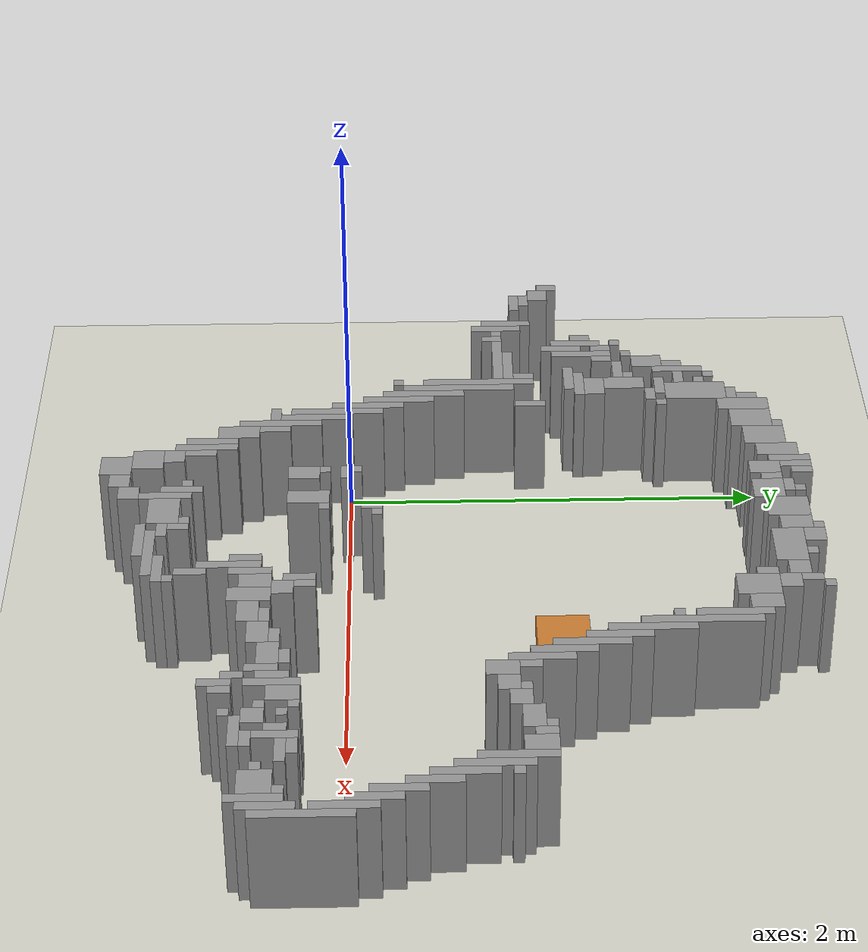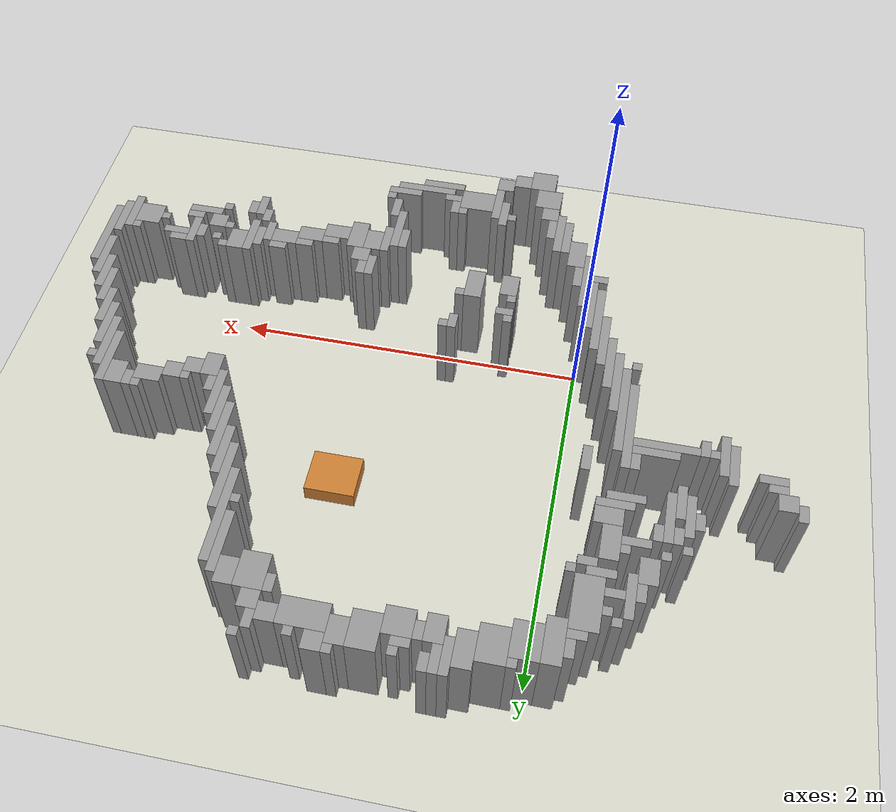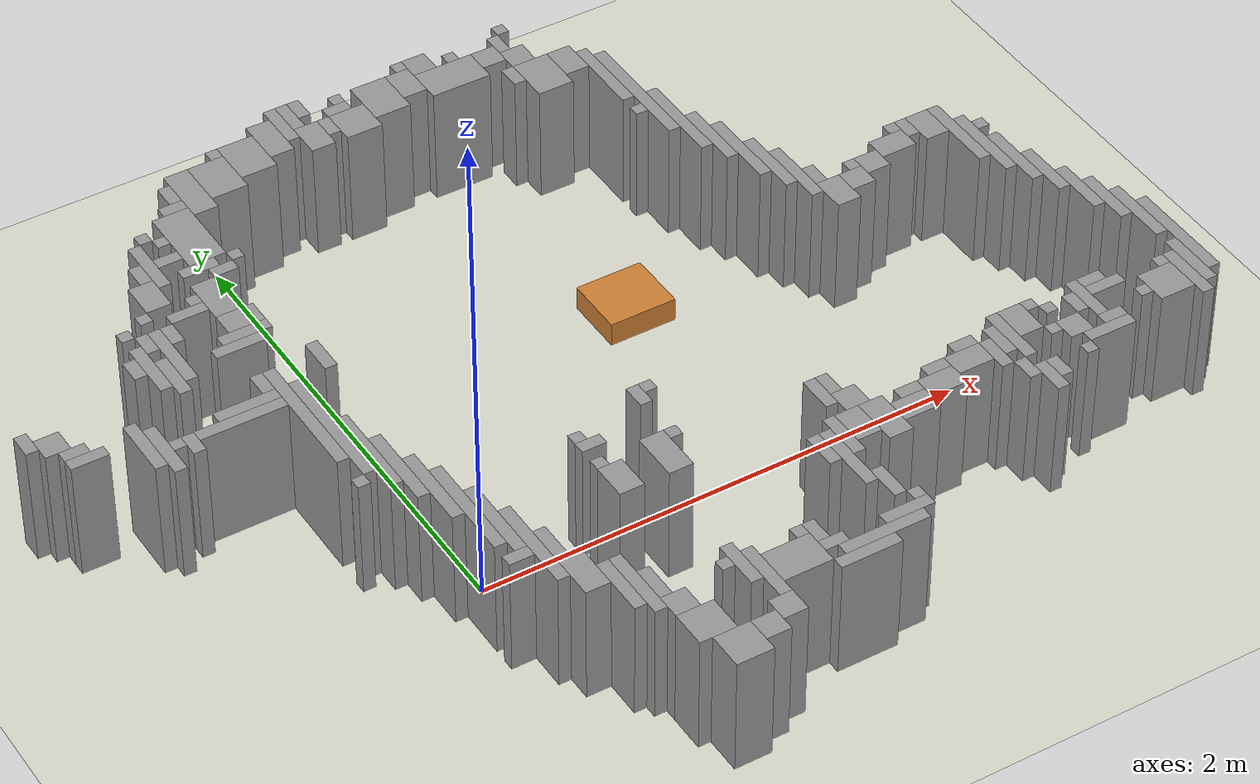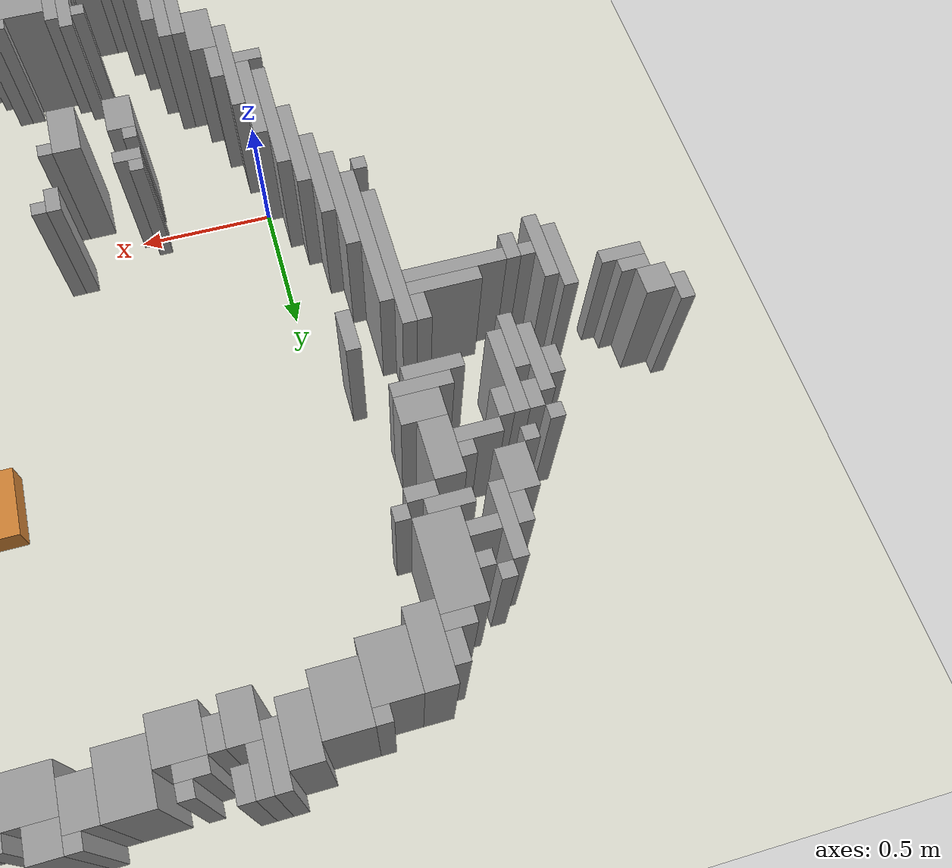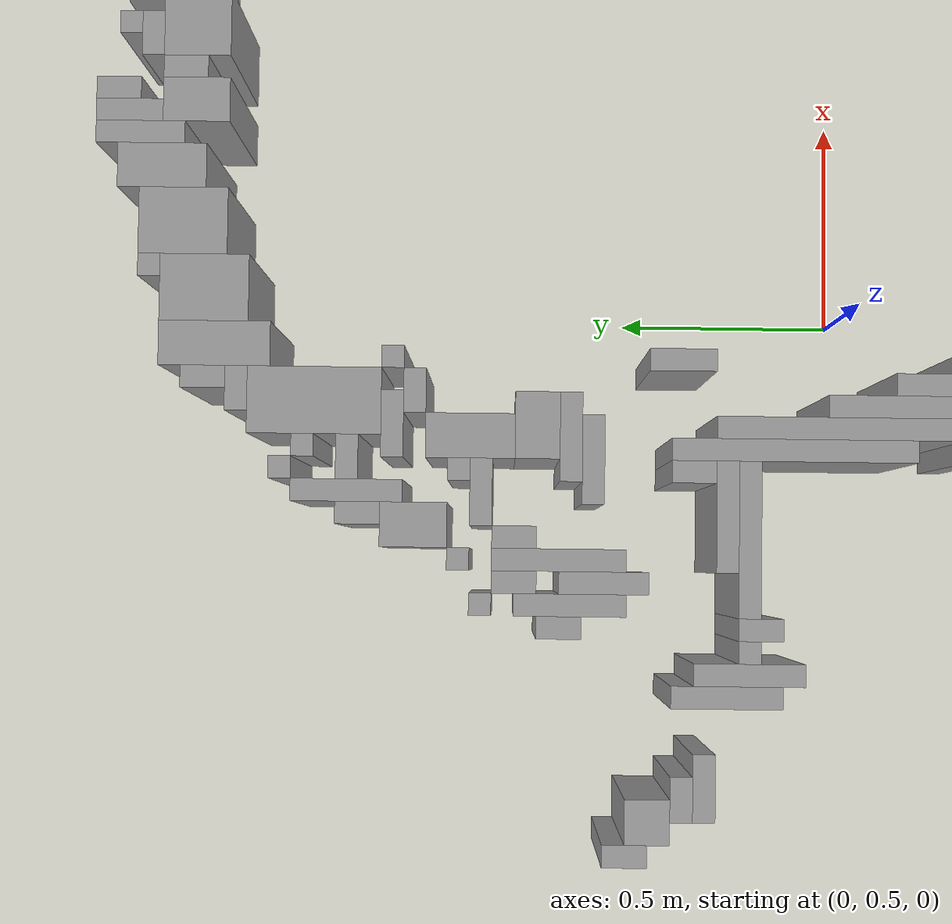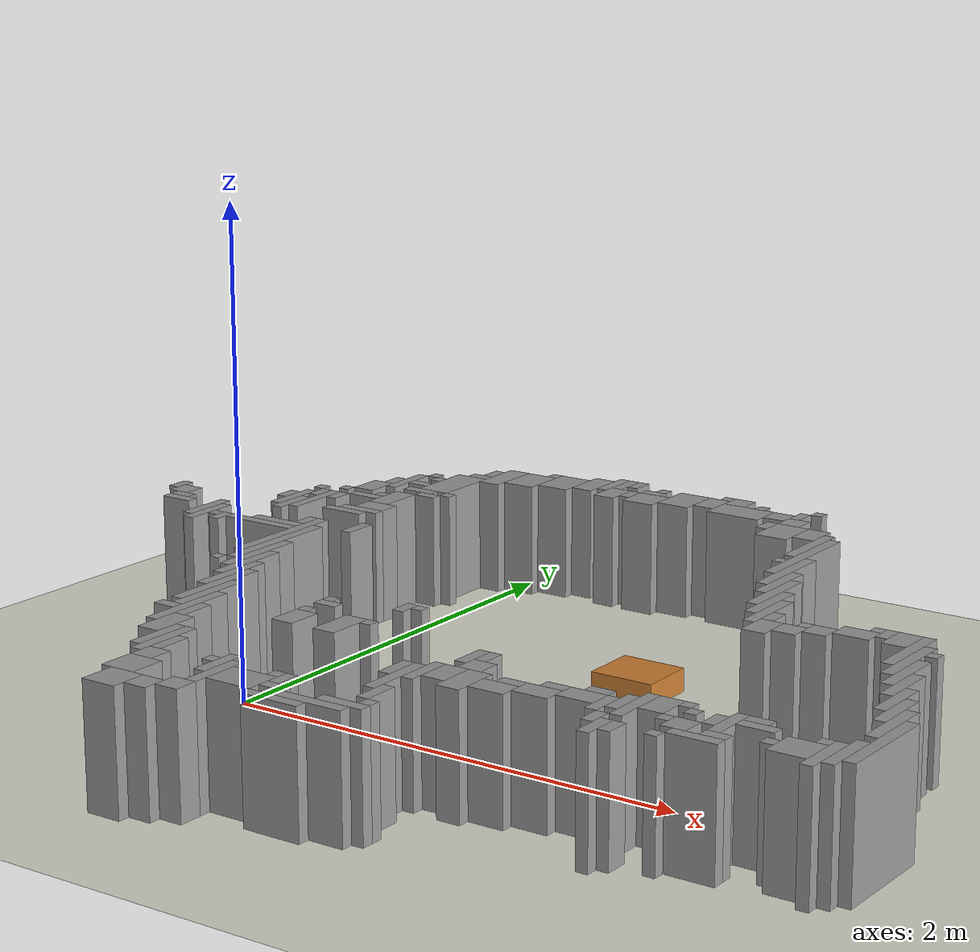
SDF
<?xml version="1.0"?>
<!-- GENERATED by jetrover_gazebo/scripts/map_to_world.py from lap2_20261005.yaml
     (737 occupied cells -> 167 wall boxes, height 0.5 m). Map frame = world frame. -->
<sdf version="1.9">
  <world name="jetrover_room">
    <physics name="1ms" type="ignored">
      <max_step_size>0.001</max_step_size>
      <real_time_factor>1.0</real_time_factor>
    </physics>
    <plugin filename="gz-sim-physics-system" name="gz::sim::systems::Physics"/>
    <plugin filename="gz-sim-user-commands-system" name="gz::sim::systems::UserCommands"/>
    <plugin filename="gz-sim-scene-broadcaster-system"
            name="gz::sim::systems::SceneBroadcaster"/>
    <plugin filename="gz-sim-sensors-system" name="gz::sim::systems::Sensors">
      <render_engine>ogre2</render_engine>
    </plugin>
    <plugin filename="gz-sim-imu-system" name="gz::sim::systems::Imu"/>
    <light type="directional" name="sun">
      <cast_shadows>true</cast_shadows>
      <pose>0 0 10 0 0 0</pose>
      <diffuse>0.8 0.8 0.8 1</diffuse>
      <specular>0.2 0.2 0.2 1</specular>
      <direction>-0.5 0.1 -0.9</direction>
    </light>
    <model name="ground_plane">
      <static>true</static>
      <link name="link">
        <collision name="c">
          <geometry><plane><normal>0 0 1</normal><size>20 20</size></plane></geometry>
          <surface><friction><ode><mu>1.0</mu><mu2>1.0</mu2></ode></friction></surface>
        </collision>
        <visual name="v">
          <geometry><plane><normal>0 0 1</normal><size>20 20</size></plane></geometry>
          <material><ambient>0.85 0.85 0.8 1</ambient><diffuse>0.85 0.85 0.8 1</diffuse></material>
        </visual>
      </link>
    </model>
    <model name="walls">
      <static>true</static>
      <link name="w0">
        <pose>0.3710 -1.1090 0.2500 0 0 0</pose>
        <collision name="c"><geometry><box><size>0.1500 0.1500 0.5000</size></box></geometry></collision>
        <visual name="v"><geometry><box><size>0.1500 0.1500 0.5000</size></box></geometry>
          <material><ambient>0.6 0.6 0.6 1</ambient><diffuse>0.6 0.6 0.6 1</diffuse></material>
        </visual>
      </link>
      <link name="w1">
        <pose>0.4960 -1.0840 0.2500 0 0 0</pose>
        <collision name="c"><geometry><box><size>0.1000 0.1000 0.5000</size></box></geometry></collision>
        <visual name="v"><geometry><box><size>0.1000 0.1000 0.5000</size></box></geometry>
          <material><ambient>0.6 0.6 0.6 1</ambient><diffuse>0.6 0.6 0.6 1</diffuse></material>
        </visual>
      </link>
      <link name="w2">
        <pose>0.5960 -1.0340 0.2500 0 0 0</pose>
        <collision name="c"><geometry><box><size>0.1000 0.1000 0.5000</size></box></geometry></collision>
        <visual name="v"><geometry><box><size>0.1000 0.1000 0.5000</size></box></geometry>
          <material><ambient>0.6 0.6 0.6 1</ambient><diffuse>0.6 0.6 0.6 1</diffuse></material>
        </visual>
      </link>
      <link name="w3">
        <pose>0.3210 -0.9590 0.2500 0 0 0</pose>
        <collision name="c"><geometry><box><size>0.1500 0.1500 0.5000</size></box></geometry></collision>
        <visual name="v"><geometry><box><size>0.1500 0.1500 0.5000</size></box></geometry>
          <material><ambient>0.6 0.6 0.6 1</ambient><diffuse>0.6 0.6 0.6 1</diffuse></material>
        </visual>
      </link>
      <link name="w4">
        <pose>0.6210 -0.8590 0.2500 0 0 0</pose>
        <collision name="c"><geometry><box><size>0.0500 0.2500 0.5000</size></box></geometry></collision>
        <visual name="v"><geometry><box><size>0.0500 0.2500 0.5000</size></box></geometry>
          <material><ambient>0.6 0.6 0.6 1</ambient><diffuse>0.6 0.6 0.6 1</diffuse></material>
        </visual>
      </link>
      <link name="w5">
        <pose>0.9710 -0.9590 0.2500 0 0 0</pose>
        <collision name="c"><geometry><box><size>0.2500 0.0500 0.5000</size></box></geometry></collision>
        <visual name="v"><geometry><box><size>0.2500 0.0500 0.5000</size></box></geometry>
          <material><ambient>0.6 0.6 0.6 1</ambient><diffuse>0.6 0.6 0.6 1</diffuse></material>
        </visual>
      </link>
      <link name="w6">
        <pose>0.7460 -0.8590 0.2500 0 0 0</pose>
        <collision name="c"><geometry><box><size>0.2000 0.1500 0.5000</size></box></geometry></collision>
        <visual name="v"><geometry><box><size>0.2000 0.1500 0.5000</size></box></geometry>
          <material><ambient>0.6 0.6 0.6 1</ambient><diffuse>0.6 0.6 0.6 1</diffuse></material>
        </visual>
      </link>
      <link name="w7">
        <pose>1.0710 -0.9090 0.2500 0 0 0</pose>
        <collision name="c"><geometry><box><size>0.3500 0.0500 0.5000</size></box></geometry></collision>
        <visual name="v"><geometry><box><size>0.3500 0.0500 0.5000</size></box></geometry>
          <material><ambient>0.6 0.6 0.6 1</ambient><diffuse>0.6 0.6 0.6 1</diffuse></material>
        </visual>
      </link>
      <link name="w8">
        <pose>0.2960 -0.8340 0.2500 0 0 0</pose>
        <collision name="c"><geometry><box><size>0.1000 0.1000 0.5000</size></box></geometry></collision>
        <visual name="v"><geometry><box><size>0.1000 0.1000 0.5000</size></box></geometry>
          <material><ambient>0.6 0.6 0.6 1</ambient><diffuse>0.6 0.6 0.6 1</diffuse></material>
        </visual>
      </link>
      <link name="w9">
        <pose>0.5710 -0.7840 0.2500 0 0 0</pose>
        <collision name="c"><geometry><box><size>0.0500 0.2000 0.5000</size></box></geometry></collision>
        <visual name="v"><geometry><box><size>0.0500 0.2000 0.5000</size></box></geometry>
          <material><ambient>0.6 0.6 0.6 1</ambient><diffuse>0.6 0.6 0.6 1</diffuse></material>
        </visual>
      </link>
      <link name="w10">
        <pose>0.8960 -0.8590 0.2500 0 0 0</pose>
        <collision name="c"><geometry><box><size>0.1000 0.0500 0.5000</size></box></geometry></collision>
        <visual name="v"><geometry><box><size>0.1000 0.0500 0.5000</size></box></geometry>
          <material><ambient>0.6 0.6 0.6 1</ambient><diffuse>0.6 0.6 0.6 1</diffuse></material>
        </visual>
      </link>
      <link name="w11">
        <pose>1.1960 -0.8590 0.2500 0 0 0</pose>
        <collision name="c"><geometry><box><size>0.2000 0.0500 0.5000</size></box></geometry></collision>
        <visual name="v"><geometry><box><size>0.2000 0.0500 0.5000</size></box></geometry>
          <material><ambient>0.6 0.6 0.6 1</ambient><diffuse>0.6 0.6 0.6 1</diffuse></material>
        </visual>
      </link>
      <link name="w12">
        <pose>0.2210 -0.6840 0.2500 0 0 0</pose>
        <collision name="c"><geometry><box><size>0.0500 0.3000 0.5000</size></box></geometry></collision>
        <visual name="v"><geometry><box><size>0.0500 0.3000 0.5000</size></box></geometry>
          <material><ambient>0.6 0.6 0.6 1</ambient><diffuse>0.6 0.6 0.6 1</diffuse></material>
        </visual>
      </link>
      <link name="w13">
        <pose>0.8710 -0.7840 0.2500 0 0 0</pose>
        <collision name="c"><geometry><box><size>0.0500 0.1000 0.5000</size></box></geometry></collision>
        <visual name="v"><geometry><box><size>0.0500 0.1000 0.5000</size></box></geometry>
          <material><ambient>0.6 0.6 0.6 1</ambient><diffuse>0.6 0.6 0.6 1</diffuse></material>
        </visual>
      </link>
      <link name="w14">
        <pose>1.2710 -0.8090 0.2500 0 0 0</pose>
        <collision name="c"><geometry><box><size>0.0500 0.0500 0.5000</size></box></geometry></collision>
        <visual name="v"><geometry><box><size>0.0500 0.0500 0.5000</size></box></geometry>
          <material><ambient>0.6 0.6 0.6 1</ambient><diffuse>0.6 0.6 0.6 1</diffuse></material>
        </visual>
      </link>
      <link name="w15">
        <pose>0.1710 -0.6590 0.2500 0 0 0</pose>
        <collision name="c"><geometry><box><size>0.0500 0.2500 0.5000</size></box></geometry></collision>
        <visual name="v"><geometry><box><size>0.0500 0.2500 0.5000</size></box></geometry>
          <material><ambient>0.6 0.6 0.6 1</ambient><diffuse>0.6 0.6 0.6 1</diffuse></material>
        </visual>
      </link>
      <link name="w16">
        <pose>0.2710 -0.7090 0.2500 0 0 0</pose>
        <collision name="c"><geometry><box><size>0.0500 0.1500 0.5000</size></box></geometry></collision>
        <visual name="v"><geometry><box><size>0.0500 0.1500 0.5000</size></box></geometry>
          <material><ambient>0.6 0.6 0.6 1</ambient><diffuse>0.6 0.6 0.6 1</diffuse></material>
        </visual>
      </link>
      <link name="w17">
        <pose>0.5210 -0.7590 0.2500 0 0 0</pose>
        <collision name="c"><geometry><box><size>0.0500 0.0500 0.5000</size></box></geometry></collision>
        <visual name="v"><geometry><box><size>0.0500 0.0500 0.5000</size></box></geometry>
          <material><ambient>0.6 0.6 0.6 1</ambient><diffuse>0.6 0.6 0.6 1</diffuse></material>
        </visual>
      </link>
      <link name="w18">
        <pose>0.8210 -0.7590 0.2500 0 0 0</pose>
        <collision name="c"><geometry><box><size>0.0500 0.0500 0.5000</size></box></geometry></collision>
        <visual name="v"><geometry><box><size>0.0500 0.0500 0.5000</size></box></geometry>
          <material><ambient>0.6 0.6 0.6 1</ambient><diffuse>0.6 0.6 0.6 1</diffuse></material>
        </visual>
      </link>
      <link name="w19">
        <pose>1.2210 -0.7090 0.2500 0 0 0</pose>
        <collision name="c"><geometry><box><size>0.0500 0.1500 0.5000</size></box></geometry></collision>
        <visual name="v"><geometry><box><size>0.0500 0.1500 0.5000</size></box></geometry>
          <material><ambient>0.6 0.6 0.6 1</ambient><diffuse>0.6 0.6 0.6 1</diffuse></material>
        </visual>
      </link>
      <link name="w20">
        <pose>1.1710 -0.5340 0.2500 0 0 0</pose>
        <collision name="c"><geometry><box><size>0.0500 0.3000 0.5000</size></box></geometry></collision>
        <visual name="v"><geometry><box><size>0.0500 0.3000 0.5000</size></box></geometry>
          <material><ambient>0.6 0.6 0.6 1</ambient><diffuse>0.6 0.6 0.6 1</diffuse></material>
        </visual>
      </link>
      <link name="w21">
        <pose>0.0960 -0.5340 0.2500 0 0 0</pose>
        <collision name="c"><geometry><box><size>0.1000 0.2000 0.5000</size></box></geometry></collision>
        <visual name="v"><geometry><box><size>0.1000 0.2000 0.5000</size></box></geometry>
          <material><ambient>0.6 0.6 0.6 1</ambient><diffuse>0.6 0.6 0.6 1</diffuse></material>
        </visual>
      </link>
      <link name="w22">
        <pose>2.0210 -0.5590 0.2500 0 0 0</pose>
        <collision name="c"><geometry><box><size>0.0500 0.1500 0.5000</size></box></geometry></collision>
        <visual name="v"><geometry><box><size>0.0500 0.1500 0.5000</size></box></geometry>
          <material><ambient>0.6 0.6 0.6 1</ambient><diffuse>0.6 0.6 0.6 1</diffuse></material>
        </visual>
      </link>
      <link name="w23">
        <pose>2.0710 -0.5340 0.2500 0 0 0</pose>
        <collision name="c"><geometry><box><size>0.0500 0.1000 0.5000</size></box></geometry></collision>
        <visual name="v"><geometry><box><size>0.0500 0.1000 0.5000</size></box></geometry>
          <material><ambient>0.6 0.6 0.6 1</ambient><diffuse>0.6 0.6 0.6 1</diffuse></material>
        </visual>
      </link>
      <link name="w24">
        <pose>0.0210 -0.3340 0.2500 0 0 0</pose>
        <collision name="c"><geometry><box><size>0.0500 0.4000 0.5000</size></box></geometry></collision>
        <visual name="v"><geometry><box><size>0.0500 0.4000 0.5000</size></box></geometry>
          <material><ambient>0.6 0.6 0.6 1</ambient><diffuse>0.6 0.6 0.6 1</diffuse></material>
        </visual>
      </link>
      <link name="w25">
        <pose>1.1210 -0.4590 0.2500 0 0 0</pose>
        <collision name="c"><geometry><box><size>0.0500 0.1500 0.5000</size></box></geometry></collision>
        <visual name="v"><geometry><box><size>0.0500 0.1500 0.5000</size></box></geometry>
          <material><ambient>0.6 0.6 0.6 1</ambient><diffuse>0.6 0.6 0.6 1</diffuse></material>
        </visual>
      </link>
      <link name="w26">
        <pose>1.2210 -0.4340 0.2500 0 0 0</pose>
        <collision name="c"><geometry><box><size>0.0500 0.2000 0.5000</size></box></geometry></collision>
        <visual name="v"><geometry><box><size>0.0500 0.2000 0.5000</size></box></geometry>
          <material><ambient>0.6 0.6 0.6 1</ambient><diffuse>0.6 0.6 0.6 1</diffuse></material>
        </visual>
      </link>
      <link name="w27">
        <pose>1.3960 -0.4340 0.2500 0 0 0</pose>
        <collision name="c"><geometry><box><size>0.1000 0.2000 0.5000</size></box></geometry></collision>
        <visual name="v"><geometry><box><size>0.1000 0.2000 0.5000</size></box></geometry>
          <material><ambient>0.6 0.6 0.6 1</ambient><diffuse>0.6 0.6 0.6 1</diffuse></material>
        </visual>
      </link>
      <link name="w28">
        <pose>1.9710 -0.4840 0.2500 0 0 0</pose>
        <collision name="c"><geometry><box><size>0.0500 0.1000 0.5000</size></box></geometry></collision>
        <visual name="v"><geometry><box><size>0.0500 0.1000 0.5000</size></box></geometry>
          <material><ambient>0.6 0.6 0.6 1</ambient><diffuse>0.6 0.6 0.6 1</diffuse></material>
        </visual>
      </link>
      <link name="w29">
        <pose>2.2210 -0.5090 0.2500 0 0 0</pose>
        <collision name="c"><geometry><box><size>0.0500 0.0500 0.5000</size></box></geometry></collision>
        <visual name="v"><geometry><box><size>0.0500 0.0500 0.5000</size></box></geometry>
          <material><ambient>0.6 0.6 0.6 1</ambient><diffuse>0.6 0.6 0.6 1</diffuse></material>
        </visual>
      </link>
      <link name="w30">
        <pose>1.2960 -0.4090 0.2500 0 0 0</pose>
        <collision name="c"><geometry><box><size>0.1000 0.1500 0.5000</size></box></geometry></collision>
        <visual name="v"><geometry><box><size>0.1000 0.1500 0.5000</size></box></geometry>
          <material><ambient>0.6 0.6 0.6 1</ambient><diffuse>0.6 0.6 0.6 1</diffuse></material>
        </visual>
      </link>
      <link name="w31">
        <pose>1.5210 -0.4340 0.2500 0 0 0</pose>
        <collision name="c"><geometry><box><size>0.1500 0.1000 0.5000</size></box></geometry></collision>
        <visual name="v"><geometry><box><size>0.1500 0.1000 0.5000</size></box></geometry>
          <material><ambient>0.6 0.6 0.6 1</ambient><diffuse>0.6 0.6 0.6 1</diffuse></material>
        </visual>
      </link>
      <link name="w32">
        <pose>2.3460 -0.4590 0.2500 0 0 0</pose>
        <collision name="c"><geometry><box><size>0.2000 0.0500 0.5000</size></box></geometry></collision>
        <visual name="v"><geometry><box><size>0.2000 0.0500 0.5000</size></box></geometry>
          <material><ambient>0.6 0.6 0.6 1</ambient><diffuse>0.6 0.6 0.6 1</diffuse></material>
        </visual>
      </link>
      <link name="w33">
        <pose>2.7710 -0.3590 0.2500 0 0 0</pose>
        <collision name="c"><geometry><box><size>0.0500 0.2500 0.5000</size></box></geometry></collision>
        <visual name="v"><geometry><box><size>0.0500 0.2500 0.5000</size></box></geometry>
          <material><ambient>0.6 0.6 0.6 1</ambient><diffuse>0.6 0.6 0.6 1</diffuse></material>
        </visual>
      </link>
      <link name="w34">
        <pose>0.0710 -0.3590 0.2500 0 0 0</pose>
        <collision name="c"><geometry><box><size>0.0500 0.1500 0.5000</size></box></geometry></collision>
        <visual name="v"><geometry><box><size>0.0500 0.1500 0.5000</size></box></geometry>
          <material><ambient>0.6 0.6 0.6 1</ambient><diffuse>0.6 0.6 0.6 1</diffuse></material>
        </visual>
      </link>
      <link name="w35">
        <pose>1.6710 -0.3840 0.2500 0 0 0</pose>
        <collision name="c"><geometry><box><size>0.1500 0.1000 0.5000</size></box></geometry></collision>
        <visual name="v"><geometry><box><size>0.1500 0.1000 0.5000</size></box></geometry>
          <material><ambient>0.6 0.6 0.6 1</ambient><diffuse>0.6 0.6 0.6 1</diffuse></material>
        </visual>
      </link>
      <link name="w36">
        <pose>1.9210 -0.3590 0.2500 0 0 0</pose>
        <collision name="c"><geometry><box><size>0.0500 0.1500 0.5000</size></box></geometry></collision>
        <visual name="v"><geometry><box><size>0.0500 0.1500 0.5000</size></box></geometry>
          <material><ambient>0.6 0.6 0.6 1</ambient><diffuse>0.6 0.6 0.6 1</diffuse></material>
        </visual>
      </link>
      <link name="w37">
        <pose>2.0210 -0.3090 0.2500 0 0 0</pose>
        <collision name="c"><geometry><box><size>0.0500 0.2500 0.5000</size></box></geometry></collision>
        <visual name="v"><geometry><box><size>0.0500 0.2500 0.5000</size></box></geometry>
          <material><ambient>0.6 0.6 0.6 1</ambient><diffuse>0.6 0.6 0.6 1</diffuse></material>
        </visual>
      </link>
      <link name="w38">
        <pose>2.2460 -0.3840 0.2500 0 0 0</pose>
        <collision name="c"><geometry><box><size>0.1000 0.1000 0.5000</size></box></geometry></collision>
        <visual name="v"><geometry><box><size>0.1000 0.1000 0.5000</size></box></geometry>
          <material><ambient>0.6 0.6 0.6 1</ambient><diffuse>0.6 0.6 0.6 1</diffuse></material>
        </visual>
      </link>
      <link name="w39">
        <pose>2.3960 -0.4090 0.2500 0 0 0</pose>
        <collision name="c"><geometry><box><size>0.1000 0.0500 0.5000</size></box></geometry></collision>
        <visual name="v"><geometry><box><size>0.1000 0.0500 0.5000</size></box></geometry>
          <material><ambient>0.6 0.6 0.6 1</ambient><diffuse>0.6 0.6 0.6 1</diffuse></material>
        </visual>
      </link>
      <link name="w40">
        <pose>2.6710 -0.3590 0.2500 0 0 0</pose>
        <collision name="c"><geometry><box><size>0.1500 0.1500 0.5000</size></box></geometry></collision>
        <visual name="v"><geometry><box><size>0.1500 0.1500 0.5000</size></box></geometry>
          <material><ambient>0.6 0.6 0.6 1</ambient><diffuse>0.6 0.6 0.6 1</diffuse></material>
        </visual>
      </link>
      <link name="w41">
        <pose>2.8210 -0.3090 0.2500 0 0 0</pose>
        <collision name="c"><geometry><box><size>0.0500 0.2500 0.5000</size></box></geometry></collision>
        <visual name="v"><geometry><box><size>0.0500 0.2500 0.5000</size></box></geometry>
          <material><ambient>0.6 0.6 0.6 1</ambient><diffuse>0.6 0.6 0.6 1</diffuse></material>
        </visual>
      </link>
      <link name="w42">
        <pose>-0.0540 -0.3590 0.2500 0 0 0</pose>
        <collision name="c"><geometry><box><size>0.1000 0.0500 0.5000</size></box></geometry></collision>
        <visual name="v"><geometry><box><size>0.1000 0.0500 0.5000</size></box></geometry>
          <material><ambient>0.6 0.6 0.6 1</ambient><diffuse>0.6 0.6 0.6 1</diffuse></material>
        </visual>
      </link>
      <link name="w43">
        <pose>1.5460 -0.3590 0.2500 0 0 0</pose>
        <collision name="c"><geometry><box><size>0.1000 0.0500 0.5000</size></box></geometry></collision>
        <visual name="v"><geometry><box><size>0.1000 0.0500 0.5000</size></box></geometry>
          <material><ambient>0.6 0.6 0.6 1</ambient><diffuse>0.6 0.6 0.6 1</diffuse></material>
        </visual>
      </link>
      <link name="w44">
        <pose>1.8210 -0.3340 0.2500 0 0 0</pose>
        <collision name="c"><geometry><box><size>0.1500 0.1000 0.5000</size></box></geometry></collision>
        <visual name="v"><geometry><box><size>0.1500 0.1000 0.5000</size></box></geometry>
          <material><ambient>0.6 0.6 0.6 1</ambient><diffuse>0.6 0.6 0.6 1</diffuse></material>
        </visual>
      </link>
      <link name="w45">
        <pose>1.9710 -0.3090 0.2500 0 0 0</pose>
        <collision name="c"><geometry><box><size>0.0500 0.1500 0.5000</size></box></geometry></collision>
        <visual name="v"><geometry><box><size>0.0500 0.1500 0.5000</size></box></geometry>
          <material><ambient>0.6 0.6 0.6 1</ambient><diffuse>0.6 0.6 0.6 1</diffuse></material>
        </visual>
      </link>
      <link name="w46">
        <pose>2.1710 -0.3590 0.2500 0 0 0</pose>
        <collision name="c"><geometry><box><size>0.0500 0.0500 0.5000</size></box></geometry></collision>
        <visual name="v"><geometry><box><size>0.0500 0.0500 0.5000</size></box></geometry>
          <material><ambient>0.6 0.6 0.6 1</ambient><diffuse>0.6 0.6 0.6 1</diffuse></material>
        </visual>
      </link>
      <link name="w47">
        <pose>2.3710 -0.2840 0.2500 0 0 0</pose>
        <collision name="c"><geometry><box><size>0.0500 0.2000 0.5000</size></box></geometry></collision>
        <visual name="v"><geometry><box><size>0.0500 0.2000 0.5000</size></box></geometry>
          <material><ambient>0.6 0.6 0.6 1</ambient><diffuse>0.6 0.6 0.6 1</diffuse></material>
        </visual>
      </link>
      <link name="w48">
        <pose>2.5710 -0.3590 0.2500 0 0 0</pose>
        <collision name="c"><geometry><box><size>0.0500 0.0500 0.5000</size></box></geometry></collision>
        <visual name="v"><geometry><box><size>0.0500 0.0500 0.5000</size></box></geometry>
          <material><ambient>0.6 0.6 0.6 1</ambient><diffuse>0.6 0.6 0.6 1</diffuse></material>
        </visual>
      </link>
      <link name="w49">
        <pose>2.8710 -0.1590 0.2500 0 0 0</pose>
        <collision name="c"><geometry><box><size>0.0500 0.4500 0.5000</size></box></geometry></collision>
        <visual name="v"><geometry><box><size>0.0500 0.4500 0.5000</size></box></geometry>
          <material><ambient>0.6 0.6 0.6 1</ambient><diffuse>0.6 0.6 0.6 1</diffuse></material>
        </visual>
      </link>
      <link name="w50">
        <pose>-0.0290 -0.1590 0.2500 0 0 0</pose>
        <collision name="c"><geometry><box><size>0.0500 0.3500 0.5000</size></box></geometry></collision>
        <visual name="v"><geometry><box><size>0.0500 0.3500 0.5000</size></box></geometry>
          <material><ambient>0.6 0.6 0.6 1</ambient><diffuse>0.6 0.6 0.6 1</diffuse></material>
        </visual>
      </link>
      <link name="w51">
        <pose>1.3460 -0.2840 0.2500 0 0 0</pose>
        <collision name="c"><geometry><box><size>0.1000 0.1000 0.5000</size></box></geometry></collision>
        <visual name="v"><geometry><box><size>0.1000 0.1000 0.5000</size></box></geometry>
          <material><ambient>0.6 0.6 0.6 1</ambient><diffuse>0.6 0.6 0.6 1</diffuse></material>
        </visual>
      </link>
      <link name="w52">
        <pose>1.6960 -0.3090 0.2500 0 0 0</pose>
        <collision name="c"><geometry><box><size>0.1000 0.0500 0.5000</size></box></geometry></collision>
        <visual name="v"><geometry><box><size>0.1000 0.0500 0.5000</size></box></geometry>
          <material><ambient>0.6 0.6 0.6 1</ambient><diffuse>0.6 0.6 0.6 1</diffuse></material>
        </visual>
      </link>
      <link name="w53">
        <pose>2.0960 -0.2590 0.2500 0 0 0</pose>
        <collision name="c"><geometry><box><size>0.1000 0.1500 0.5000</size></box></geometry></collision>
        <visual name="v"><geometry><box><size>0.1000 0.1500 0.5000</size></box></geometry>
          <material><ambient>0.6 0.6 0.6 1</ambient><diffuse>0.6 0.6 0.6 1</diffuse></material>
        </visual>
      </link>
      <link name="w54">
        <pose>2.3210 -0.2840 0.2500 0 0 0</pose>
        <collision name="c"><geometry><box><size>0.0500 0.1000 0.5000</size></box></geometry></collision>
        <visual name="v"><geometry><box><size>0.0500 0.1000 0.5000</size></box></geometry>
          <material><ambient>0.6 0.6 0.6 1</ambient><diffuse>0.6 0.6 0.6 1</diffuse></material>
        </visual>
      </link>
      <link name="w55">
        <pose>-0.0790 -0.0590 0.2500 0 0 0</pose>
        <collision name="c"><geometry><box><size>0.0500 0.4500 0.5000</size></box></geometry></collision>
        <visual name="v"><geometry><box><size>0.0500 0.4500 0.5000</size></box></geometry>
          <material><ambient>0.6 0.6 0.6 1</ambient><diffuse>0.6 0.6 0.6 1</diffuse></material>
        </visual>
      </link>
      <link name="w56">
        <pose>0.4460 -0.2090 0.2500 0 0 0</pose>
        <collision name="c"><geometry><box><size>0.1000 0.1500 0.5000</size></box></geometry></collision>
        <visual name="v"><geometry><box><size>0.1000 0.1500 0.5000</size></box></geometry>
          <material><ambient>0.6 0.6 0.6 1</ambient><diffuse>0.6 0.6 0.6 1</diffuse></material>
        </visual>
      </link>
      <link name="w57">
        <pose>0.6460 -0.1840 0.2500 0 0 0</pose>
        <collision name="c"><geometry><box><size>0.1000 0.2000 0.5000</size></box></geometry></collision>
        <visual name="v"><geometry><box><size>0.1000 0.2000 0.5000</size></box></geometry>
          <material><ambient>0.6 0.6 0.6 1</ambient><diffuse>0.6 0.6 0.6 1</diffuse></material>
        </visual>
      </link>
      <link name="w58">
        <pose>1.2710 -0.2090 0.2500 0 0 0</pose>
        <collision name="c"><geometry><box><size>0.0500 0.1500 0.5000</size></box></geometry></collision>
        <visual name="v"><geometry><box><size>0.0500 0.1500 0.5000</size></box></geometry>
          <material><ambient>0.6 0.6 0.6 1</ambient><diffuse>0.6 0.6 0.6 1</diffuse></material>
        </visual>
      </link>
      <link name="w59">
        <pose>1.8460 -0.2590 0.2500 0 0 0</pose>
        <collision name="c"><geometry><box><size>0.1000 0.0500 0.5000</size></box></geometry></collision>
        <visual name="v"><geometry><box><size>0.1000 0.0500 0.5000</size></box></geometry>
          <material><ambient>0.6 0.6 0.6 1</ambient><diffuse>0.6 0.6 0.6 1</diffuse></material>
        </visual>
      </link>
      <link name="w60">
        <pose>2.2210 -0.2590 0.2500 0 0 0</pose>
        <collision name="c"><geometry><box><size>0.0500 0.0500 0.5000</size></box></geometry></collision>
        <visual name="v"><geometry><box><size>0.0500 0.0500 0.5000</size></box></geometry>
          <material><ambient>0.6 0.6 0.6 1</ambient><diffuse>0.6 0.6 0.6 1</diffuse></material>
        </visual>
      </link>
      <link name="w61">
        <pose>2.4710 -0.2590 0.2500 0 0 0</pose>
        <collision name="c"><geometry><box><size>0.1500 0.0500 0.5000</size></box></geometry></collision>
        <visual name="v"><geometry><box><size>0.1500 0.0500 0.5000</size></box></geometry>
          <material><ambient>0.6 0.6 0.6 1</ambient><diffuse>0.6 0.6 0.6 1</diffuse></material>
        </visual>
      </link>
      <link name="w62">
        <pose>2.7210 -0.2590 0.2500 0 0 0</pose>
        <collision name="c"><geometry><box><size>0.0500 0.0500 0.5000</size></box></geometry></collision>
        <visual name="v"><geometry><box><size>0.0500 0.0500 0.5000</size></box></geometry>
          <material><ambient>0.6 0.6 0.6 1</ambient><diffuse>0.6 0.6 0.6 1</diffuse></material>
        </visual>
      </link>
      <link name="w63">
        <pose>1.3210 -0.1840 0.2500 0 0 0</pose>
        <collision name="c"><geometry><box><size>0.0500 0.1000 0.5000</size></box></geometry></collision>
        <visual name="v"><geometry><box><size>0.0500 0.1000 0.5000</size></box></geometry>
          <material><ambient>0.6 0.6 0.6 1</ambient><diffuse>0.6 0.6 0.6 1</diffuse></material>
        </visual>
      </link>
      <link name="w64">
        <pose>2.1710 -0.2090 0.2500 0 0 0</pose>
        <collision name="c"><geometry><box><size>0.0500 0.0500 0.5000</size></box></geometry></collision>
        <visual name="v"><geometry><box><size>0.0500 0.0500 0.5000</size></box></geometry>
          <material><ambient>0.6 0.6 0.6 1</ambient><diffuse>0.6 0.6 0.6 1</diffuse></material>
        </visual>
      </link>
      <link name="w65">
        <pose>2.4460 -0.2090 0.2500 0 0 0</pose>
        <collision name="c"><geometry><box><size>0.1000 0.0500 0.5000</size></box></geometry></collision>
        <visual name="v"><geometry><box><size>0.1000 0.0500 0.5000</size></box></geometry>
          <material><ambient>0.6 0.6 0.6 1</ambient><diffuse>0.6 0.6 0.6 1</diffuse></material>
        </visual>
      </link>
      <link name="w66">
        <pose>0.4210 -0.1090 0.2500 0 0 0</pose>
        <collision name="c"><geometry><box><size>0.0500 0.0500 0.5000</size></box></geometry></collision>
        <visual name="v"><geometry><box><size>0.0500 0.0500 0.5000</size></box></geometry>
          <material><ambient>0.6 0.6 0.6 1</ambient><diffuse>0.6 0.6 0.6 1</diffuse></material>
        </visual>
      </link>
      <link name="w67">
        <pose>0.7210 -0.1090 0.2500 0 0 0</pose>
        <collision name="c"><geometry><box><size>0.0500 0.0500 0.5000</size></box></geometry></collision>
        <visual name="v"><geometry><box><size>0.0500 0.0500 0.5000</size></box></geometry>
          <material><ambient>0.6 0.6 0.6 1</ambient><diffuse>0.6 0.6 0.6 1</diffuse></material>
        </visual>
      </link>
      <link name="w68">
        <pose>2.8210 0.0160 0.2500 0 0 0</pose>
        <collision name="c"><geometry><box><size>0.0500 0.3000 0.5000</size></box></geometry></collision>
        <visual name="v"><geometry><box><size>0.0500 0.3000 0.5000</size></box></geometry>
          <material><ambient>0.6 0.6 0.6 1</ambient><diffuse>0.6 0.6 0.6 1</diffuse></material>
        </visual>
      </link>
      <link name="w69">
        <pose>-0.1290 0.0910 0.2500 0 0 0</pose>
        <collision name="c"><geometry><box><size>0.0500 0.3500 0.5000</size></box></geometry></collision>
        <visual name="v"><geometry><box><size>0.0500 0.3500 0.5000</size></box></geometry>
          <material><ambient>0.6 0.6 0.6 1</ambient><diffuse>0.6 0.6 0.6 1</diffuse></material>
        </visual>
      </link>
      <link name="w70">
        <pose>0.4460 -0.0090 0.2500 0 0 0</pose>
        <collision name="c"><geometry><box><size>0.1000 0.0500 0.5000</size></box></geometry></collision>
        <visual name="v"><geometry><box><size>0.1000 0.0500 0.5000</size></box></geometry>
          <material><ambient>0.6 0.6 0.6 1</ambient><diffuse>0.6 0.6 0.6 1</diffuse></material>
        </visual>
      </link>
      <link name="w71">
        <pose>0.4210 0.0410 0.2500 0 0 0</pose>
        <collision name="c"><geometry><box><size>0.0500 0.0500 0.5000</size></box></geometry></collision>
        <visual name="v"><geometry><box><size>0.0500 0.0500 0.5000</size></box></geometry>
          <material><ambient>0.6 0.6 0.6 1</ambient><diffuse>0.6 0.6 0.6 1</diffuse></material>
        </visual>
      </link>
      <link name="w72">
        <pose>2.7710 0.1410 0.2500 0 0 0</pose>
        <collision name="c"><geometry><box><size>0.0500 0.2500 0.5000</size></box></geometry></collision>
        <visual name="v"><geometry><box><size>0.0500 0.2500 0.5000</size></box></geometry>
          <material><ambient>0.6 0.6 0.6 1</ambient><diffuse>0.6 0.6 0.6 1</diffuse></material>
        </visual>
      </link>
      <link name="w73">
        <pose>-0.1790 0.2410 0.2500 0 0 0</pose>
        <collision name="c"><geometry><box><size>0.0500 0.3500 0.5000</size></box></geometry></collision>
        <visual name="v"><geometry><box><size>0.0500 0.3500 0.5000</size></box></geometry>
          <material><ambient>0.6 0.6 0.6 1</ambient><diffuse>0.6 0.6 0.6 1</diffuse></material>
        </visual>
      </link>
      <link name="w74">
        <pose>0.7210 0.1160 0.2500 0 0 0</pose>
        <collision name="c"><geometry><box><size>0.0500 0.1000 0.5000</size></box></geometry></collision>
        <visual name="v"><geometry><box><size>0.0500 0.1000 0.5000</size></box></geometry>
          <material><ambient>0.6 0.6 0.6 1</ambient><diffuse>0.6 0.6 0.6 1</diffuse></material>
        </visual>
      </link>
      <link name="w75">
        <pose>0.7710 0.1410 0.2500 0 0 0</pose>
        <collision name="c"><geometry><box><size>0.0500 0.0500 0.5000</size></box></geometry></collision>
        <visual name="v"><geometry><box><size>0.0500 0.0500 0.5000</size></box></geometry>
          <material><ambient>0.6 0.6 0.6 1</ambient><diffuse>0.6 0.6 0.6 1</diffuse></material>
        </visual>
      </link>
      <link name="w76">
        <pose>2.7210 0.2410 0.2500 0 0 0</pose>
        <collision name="c"><geometry><box><size>0.0500 0.2500 0.5000</size></box></geometry></collision>
        <visual name="v"><geometry><box><size>0.0500 0.2500 0.5000</size></box></geometry>
          <material><ambient>0.6 0.6 0.6 1</ambient><diffuse>0.6 0.6 0.6 1</diffuse></material>
        </visual>
      </link>
      <link name="w77">
        <pose>-0.2290 0.3660 0.2500 0 0 0</pose>
        <collision name="c"><geometry><box><size>0.0500 0.4000 0.5000</size></box></geometry></collision>
        <visual name="v"><geometry><box><size>0.0500 0.4000 0.5000</size></box></geometry>
          <material><ambient>0.6 0.6 0.6 1</ambient><diffuse>0.6 0.6 0.6 1</diffuse></material>
        </visual>
      </link>
      <link name="w78">
        <pose>-0.3290 0.2410 0.2500 0 0 0</pose>
        <collision name="c"><geometry><box><size>0.0500 0.0500 0.5000</size></box></geometry></collision>
        <visual name="v"><geometry><box><size>0.0500 0.0500 0.5000</size></box></geometry>
          <material><ambient>0.6 0.6 0.6 1</ambient><diffuse>0.6 0.6 0.6 1</diffuse></material>
        </visual>
      </link>
      <link name="w79">
        <pose>-0.2790 0.5410 0.2500 0 0 0</pose>
        <collision name="c"><geometry><box><size>0.0500 0.5500 0.5000</size></box></geometry></collision>
        <visual name="v"><geometry><box><size>0.0500 0.5500 0.5000</size></box></geometry>
          <material><ambient>0.6 0.6 0.6 1</ambient><diffuse>0.6 0.6 0.6 1</diffuse></material>
        </visual>
      </link>
      <link name="w80">
        <pose>2.6710 0.3910 0.2500 0 0 0</pose>
        <collision name="c"><geometry><box><size>0.0500 0.2500 0.5000</size></box></geometry></collision>
        <visual name="v"><geometry><box><size>0.0500 0.2500 0.5000</size></box></geometry>
          <material><ambient>0.6 0.6 0.6 1</ambient><diffuse>0.6 0.6 0.6 1</diffuse></material>
        </visual>
      </link>
      <link name="w81">
        <pose>-0.3290 0.6410 0.2500 0 0 0</pose>
        <collision name="c"><geometry><box><size>0.0500 0.5500 0.5000</size></box></geometry></collision>
        <visual name="v"><geometry><box><size>0.0500 0.5500 0.5000</size></box></geometry>
          <material><ambient>0.6 0.6 0.6 1</ambient><diffuse>0.6 0.6 0.6 1</diffuse></material>
        </visual>
      </link>
      <link name="w82">
        <pose>2.6210 0.5160 0.2500 0 0 0</pose>
        <collision name="c"><geometry><box><size>0.0500 0.3000 0.5000</size></box></geometry></collision>
        <visual name="v"><geometry><box><size>0.0500 0.3000 0.5000</size></box></geometry>
          <material><ambient>0.6 0.6 0.6 1</ambient><diffuse>0.6 0.6 0.6 1</diffuse></material>
        </visual>
      </link>
      <link name="w83">
        <pose>2.5710 0.6410 0.2500 0 0 0</pose>
        <collision name="c"><geometry><box><size>0.0500 0.3500 0.5000</size></box></geometry></collision>
        <visual name="v"><geometry><box><size>0.0500 0.3500 0.5000</size></box></geometry>
          <material><ambient>0.6 0.6 0.6 1</ambient><diffuse>0.6 0.6 0.6 1</diffuse></material>
        </visual>
      </link>
      <link name="w84">
        <pose>2.5210 0.7410 0.2500 0 0 0</pose>
        <collision name="c"><geometry><box><size>0.0500 0.3500 0.5000</size></box></geometry></collision>
        <visual name="v"><geometry><box><size>0.0500 0.3500 0.5000</size></box></geometry>
          <material><ambient>0.6 0.6 0.6 1</ambient><diffuse>0.6 0.6 0.6 1</diffuse></material>
        </visual>
      </link>
      <link name="w85">
        <pose>-0.8290 0.7410 0.2500 0 0 0</pose>
        <collision name="c"><geometry><box><size>0.0500 0.2500 0.5000</size></box></geometry></collision>
        <visual name="v"><geometry><box><size>0.0500 0.2500 0.5000</size></box></geometry>
          <material><ambient>0.6 0.6 0.6 1</ambient><diffuse>0.6 0.6 0.6 1</diffuse></material>
        </visual>
      </link>
      <link name="w86">
        <pose>1.9460 0.6910 0.2500 0 0 0</pose>
        <collision name="c"><geometry><box><size>0.1000 0.1500 0.5000</size></box></geometry></collision>
        <visual name="v"><geometry><box><size>0.1000 0.1500 0.5000</size></box></geometry>
          <material><ambient>0.6 0.6 0.6 1</ambient><diffuse>0.6 0.6 0.6 1</diffuse></material>
        </visual>
      </link>
      <link name="w87">
        <pose>-0.8790 0.7910 0.2500 0 0 0</pose>
        <collision name="c"><geometry><box><size>0.0500 0.2500 0.5000</size></box></geometry></collision>
        <visual name="v"><geometry><box><size>0.0500 0.2500 0.5000</size></box></geometry>
          <material><ambient>0.6 0.6 0.6 1</ambient><diffuse>0.6 0.6 0.6 1</diffuse></material>
        </visual>
      </link>
      <link name="w88">
        <pose>-0.7290 0.7160 0.2500 0 0 0</pose>
        <collision name="c"><geometry><box><size>0.0500 0.1000 0.5000</size></box></geometry></collision>
        <visual name="v"><geometry><box><size>0.0500 0.1000 0.5000</size></box></geometry>
          <material><ambient>0.6 0.6 0.6 1</ambient><diffuse>0.6 0.6 0.6 1</diffuse></material>
        </visual>
      </link>
      <link name="w89">
        <pose>2.0460 0.7160 0.2500 0 0 0</pose>
        <collision name="c"><geometry><box><size>0.1000 0.1000 0.5000</size></box></geometry></collision>
        <visual name="v"><geometry><box><size>0.1000 0.1000 0.5000</size></box></geometry>
          <material><ambient>0.6 0.6 0.6 1</ambient><diffuse>0.6 0.6 0.6 1</diffuse></material>
        </visual>
      </link>
      <link name="w90">
        <pose>-0.7790 0.7410 0.2500 0 0 0</pose>
        <collision name="c"><geometry><box><size>0.0500 0.0500 0.5000</size></box></geometry></collision>
        <visual name="v"><geometry><box><size>0.0500 0.0500 0.5000</size></box></geometry>
          <material><ambient>0.6 0.6 0.6 1</ambient><diffuse>0.6 0.6 0.6 1</diffuse></material>
        </visual>
      </link>
      <link name="w91">
        <pose>-0.5290 0.7410 0.2500 0 0 0</pose>
        <collision name="c"><geometry><box><size>0.3500 0.0500 0.5000</size></box></geometry></collision>
        <visual name="v"><geometry><box><size>0.3500 0.0500 0.5000</size></box></geometry>
          <material><ambient>0.6 0.6 0.6 1</ambient><diffuse>0.6 0.6 0.6 1</diffuse></material>
        </visual>
      </link>
      <link name="w92">
        <pose>1.8710 0.8660 0.2500 0 0 0</pose>
        <collision name="c"><geometry><box><size>0.0500 0.3000 0.5000</size></box></geometry></collision>
        <visual name="v"><geometry><box><size>0.0500 0.3000 0.5000</size></box></geometry>
          <material><ambient>0.6 0.6 0.6 1</ambient><diffuse>0.6 0.6 0.6 1</diffuse></material>
        </visual>
      </link>
      <link name="w93">
        <pose>2.1460 0.7660 0.2500 0 0 0</pose>
        <collision name="c"><geometry><box><size>0.1000 0.1000 0.5000</size></box></geometry></collision>
        <visual name="v"><geometry><box><size>0.1000 0.1000 0.5000</size></box></geometry>
          <material><ambient>0.6 0.6 0.6 1</ambient><diffuse>0.6 0.6 0.6 1</diffuse></material>
        </visual>
      </link>
      <link name="w94">
        <pose>2.6210 0.7410 0.2500 0 0 0</pose>
        <collision name="c"><geometry><box><size>0.0500 0.0500 0.5000</size></box></geometry></collision>
        <visual name="v"><geometry><box><size>0.0500 0.0500 0.5000</size></box></geometry>
          <material><ambient>0.6 0.6 0.6 1</ambient><diffuse>0.6 0.6 0.6 1</diffuse></material>
        </visual>
      </link>
      <link name="w95">
        <pose>-0.4790 0.7910 0.2500 0 0 0</pose>
        <collision name="c"><geometry><box><size>0.2500 0.0500 0.5000</size></box></geometry></collision>
        <visual name="v"><geometry><box><size>0.2500 0.0500 0.5000</size></box></geometry>
          <material><ambient>0.6 0.6 0.6 1</ambient><diffuse>0.6 0.6 0.6 1</diffuse></material>
        </visual>
      </link>
      <link name="w96">
        <pose>1.9210 0.8160 0.2500 0 0 0</pose>
        <collision name="c"><geometry><box><size>0.0500 0.1000 0.5000</size></box></geometry></collision>
        <visual name="v"><geometry><box><size>0.0500 0.1000 0.5000</size></box></geometry>
          <material><ambient>0.6 0.6 0.6 1</ambient><diffuse>0.6 0.6 0.6 1</diffuse></material>
        </visual>
      </link>
      <link name="w97">
        <pose>2.0710 0.7910 0.2500 0 0 0</pose>
        <collision name="c"><geometry><box><size>0.0500 0.0500 0.5000</size></box></geometry></collision>
        <visual name="v"><geometry><box><size>0.0500 0.0500 0.5000</size></box></geometry>
          <material><ambient>0.6 0.6 0.6 1</ambient><diffuse>0.6 0.6 0.6 1</diffuse></material>
        </visual>
      </link>
      <link name="w98">
        <pose>2.2710 0.8160 0.2500 0 0 0</pose>
        <collision name="c"><geometry><box><size>0.1500 0.1000 0.5000</size></box></geometry></collision>
        <visual name="v"><geometry><box><size>0.1500 0.1000 0.5000</size></box></geometry>
          <material><ambient>0.6 0.6 0.6 1</ambient><diffuse>0.6 0.6 0.6 1</diffuse></material>
        </visual>
      </link>
      <link name="w99">
        <pose>2.4460 0.8410 0.2500 0 0 0</pose>
        <collision name="c"><geometry><box><size>0.1000 0.1500 0.5000</size></box></geometry></collision>
        <visual name="v"><geometry><box><size>0.1000 0.1500 0.5000</size></box></geometry>
          <material><ambient>0.6 0.6 0.6 1</ambient><diffuse>0.6 0.6 0.6 1</diffuse></material>
        </visual>
      </link>
      <link name="w100">
        <pose>-1.0790 0.8410 0.2500 0 0 0</pose>
        <collision name="c"><geometry><box><size>0.1500 0.0500 0.5000</size></box></geometry></collision>
        <visual name="v"><geometry><box><size>0.1500 0.0500 0.5000</size></box></geometry>
          <material><ambient>0.6 0.6 0.6 1</ambient><diffuse>0.6 0.6 0.6 1</diffuse></material>
        </visual>
      </link>
      <link name="w101">
        <pose>-0.3790 0.8660 0.2500 0 0 0</pose>
        <collision name="c"><geometry><box><size>0.0500 0.1000 0.5000</size></box></geometry></collision>
        <visual name="v"><geometry><box><size>0.0500 0.1000 0.5000</size></box></geometry>
          <material><ambient>0.6 0.6 0.6 1</ambient><diffuse>0.6 0.6 0.6 1</diffuse></material>
        </visual>
      </link>
      <link name="w102">
        <pose>-0.1290 0.8910 0.2500 0 0 0</pose>
        <collision name="c"><geometry><box><size>0.0500 0.1500 0.5000</size></box></geometry></collision>
        <visual name="v"><geometry><box><size>0.0500 0.1500 0.5000</size></box></geometry>
          <material><ambient>0.6 0.6 0.6 1</ambient><diffuse>0.6 0.6 0.6 1</diffuse></material>
        </visual>
      </link>
      <link name="w103">
        <pose>1.8210 0.9660 0.2500 0 0 0</pose>
        <collision name="c"><geometry><box><size>0.0500 0.3000 0.5000</size></box></geometry></collision>
        <visual name="v"><geometry><box><size>0.0500 0.3000 0.5000</size></box></geometry>
          <material><ambient>0.6 0.6 0.6 1</ambient><diffuse>0.6 0.6 0.6 1</diffuse></material>
        </visual>
      </link>
      <link name="w104">
        <pose>2.3710 0.8660 0.2500 0 0 0</pose>
        <collision name="c"><geometry><box><size>0.0500 0.1000 0.5000</size></box></geometry></collision>
        <visual name="v"><geometry><box><size>0.0500 0.1000 0.5000</size></box></geometry>
          <material><ambient>0.6 0.6 0.6 1</ambient><diffuse>0.6 0.6 0.6 1</diffuse></material>
        </visual>
      </link>
      <link name="w105">
        <pose>-1.1040 0.8910 0.2500 0 0 0</pose>
        <collision name="c"><geometry><box><size>0.1000 0.0500 0.5000</size></box></geometry></collision>
        <visual name="v"><geometry><box><size>0.1000 0.0500 0.5000</size></box></geometry>
          <material><ambient>0.6 0.6 0.6 1</ambient><diffuse>0.6 0.6 0.6 1</diffuse></material>
        </visual>
      </link>
      <link name="w106">
        <pose>2.3210 0.8910 0.2500 0 0 0</pose>
        <collision name="c"><geometry><box><size>0.0500 0.0500 0.5000</size></box></geometry></collision>
        <visual name="v"><geometry><box><size>0.0500 0.0500 0.5000</size></box></geometry>
          <material><ambient>0.6 0.6 0.6 1</ambient><diffuse>0.6 0.6 0.6 1</diffuse></material>
        </visual>
      </link>
      <link name="w107">
        <pose>-1.1540 0.9660 0.2500 0 0 0</pose>
        <collision name="c"><geometry><box><size>0.1000 0.1000 0.5000</size></box></geometry></collision>
        <visual name="v"><geometry><box><size>0.1000 0.1000 0.5000</size></box></geometry>
          <material><ambient>0.6 0.6 0.6 1</ambient><diffuse>0.6 0.6 0.6 1</diffuse></material>
        </visual>
      </link>
      <link name="w108">
        <pose>1.7710 1.0910 0.2500 0 0 0</pose>
        <collision name="c"><geometry><box><size>0.0500 0.3500 0.5000</size></box></geometry></collision>
        <visual name="v"><geometry><box><size>0.0500 0.3500 0.5000</size></box></geometry>
          <material><ambient>0.6 0.6 0.6 1</ambient><diffuse>0.6 0.6 0.6 1</diffuse></material>
        </visual>
      </link>
      <link name="w109">
        <pose>-1.2290 1.0160 0.2500 0 0 0</pose>
        <collision name="c"><geometry><box><size>0.0500 0.1000 0.5000</size></box></geometry></collision>
        <visual name="v"><geometry><box><size>0.0500 0.1000 0.5000</size></box></geometry>
          <material><ambient>0.6 0.6 0.6 1</ambient><diffuse>0.6 0.6 0.6 1</diffuse></material>
        </visual>
      </link>
      <link name="w110">
        <pose>-0.6290 1.0660 0.2500 0 0 0</pose>
        <collision name="c"><geometry><box><size>0.0500 0.2000 0.5000</size></box></geometry></collision>
        <visual name="v"><geometry><box><size>0.0500 0.2000 0.5000</size></box></geometry>
          <material><ambient>0.6 0.6 0.6 1</ambient><diffuse>0.6 0.6 0.6 1</diffuse></material>
        </visual>
      </link>
      <link name="w111">
        <pose>-0.6790 1.1410 0.2500 0 0 0</pose>
        <collision name="c"><geometry><box><size>0.0500 0.2500 0.5000</size></box></geometry></collision>
        <visual name="v"><geometry><box><size>0.0500 0.2500 0.5000</size></box></geometry>
          <material><ambient>0.6 0.6 0.6 1</ambient><diffuse>0.6 0.6 0.6 1</diffuse></material>
        </visual>
      </link>
      <link name="w112">
        <pose>-0.5790 1.1660 0.2500 0 0 0</pose>
        <collision name="c"><geometry><box><size>0.0500 0.3000 0.5000</size></box></geometry></collision>
        <visual name="v"><geometry><box><size>0.0500 0.3000 0.5000</size></box></geometry>
          <material><ambient>0.6 0.6 0.6 1</ambient><diffuse>0.6 0.6 0.6 1</diffuse></material>
        </visual>
      </link>
      <link name="w113">
        <pose>-0.3540 1.0910 0.2500 0 0 0</pose>
        <collision name="c"><geometry><box><size>0.2000 0.0500 0.5000</size></box></geometry></collision>
        <visual name="v"><geometry><box><size>0.2000 0.0500 0.5000</size></box></geometry>
          <material><ambient>0.6 0.6 0.6 1</ambient><diffuse>0.6 0.6 0.6 1</diffuse></material>
        </visual>
      </link>
      <link name="w114">
        <pose>1.7210 1.2160 0.2500 0 0 0</pose>
        <collision name="c"><geometry><box><size>0.0500 0.3000 0.5000</size></box></geometry></collision>
        <visual name="v"><geometry><box><size>0.0500 0.3000 0.5000</size></box></geometry>
          <material><ambient>0.6 0.6 0.6 1</ambient><diffuse>0.6 0.6 0.6 1</diffuse></material>
        </visual>
      </link>
      <link name="w115">
        <pose>-0.7290 1.1660 0.2500 0 0 0</pose>
        <collision name="c"><geometry><box><size>0.0500 0.1000 0.5000</size></box></geometry></collision>
        <visual name="v"><geometry><box><size>0.0500 0.1000 0.5000</size></box></geometry>
          <material><ambient>0.6 0.6 0.6 1</ambient><diffuse>0.6 0.6 0.6 1</diffuse></material>
        </visual>
      </link>
      <link name="w116">
        <pose>-0.3040 1.1410 0.2500 0 0 0</pose>
        <collision name="c"><geometry><box><size>0.2000 0.0500 0.5000</size></box></geometry></collision>
        <visual name="v"><geometry><box><size>0.2000 0.0500 0.5000</size></box></geometry>
          <material><ambient>0.6 0.6 0.6 1</ambient><diffuse>0.6 0.6 0.6 1</diffuse></material>
        </visual>
      </link>
      <link name="w117">
        <pose>-0.2790 1.2160 0.2500 0 0 0</pose>
        <collision name="c"><geometry><box><size>0.1500 0.1000 0.5000</size></box></geometry></collision>
        <visual name="v"><geometry><box><size>0.1500 0.1000 0.5000</size></box></geometry>
          <material><ambient>0.6 0.6 0.6 1</ambient><diffuse>0.6 0.6 0.6 1</diffuse></material>
        </visual>
      </link>
      <link name="w118">
        <pose>1.6710 1.3660 0.2500 0 0 0</pose>
        <collision name="c"><geometry><box><size>0.0500 0.4000 0.5000</size></box></geometry></collision>
        <visual name="v"><geometry><box><size>0.0500 0.4000 0.5000</size></box></geometry>
          <material><ambient>0.6 0.6 0.6 1</ambient><diffuse>0.6 0.6 0.6 1</diffuse></material>
        </visual>
      </link>
      <link name="w119">
        <pose>-0.6290 1.2660 0.2500 0 0 0</pose>
        <collision name="c"><geometry><box><size>0.0500 0.1000 0.5000</size></box></geometry></collision>
        <visual name="v"><geometry><box><size>0.0500 0.1000 0.5000</size></box></geometry>
          <material><ambient>0.6 0.6 0.6 1</ambient><diffuse>0.6 0.6 0.6 1</diffuse></material>
        </visual>
      </link>
      <link name="w120">
        <pose>-0.5290 1.2660 0.2500 0 0 0</pose>
        <collision name="c"><geometry><box><size>0.0500 0.1000 0.5000</size></box></geometry></collision>
        <visual name="v"><geometry><box><size>0.0500 0.1000 0.5000</size></box></geometry>
          <material><ambient>0.6 0.6 0.6 1</ambient><diffuse>0.6 0.6 0.6 1</diffuse></material>
        </visual>
      </link>
      <link name="w121">
        <pose>-0.3040 1.3660 0.2500 0 0 0</pose>
        <collision name="c"><geometry><box><size>0.1000 0.2000 0.5000</size></box></geometry></collision>
        <visual name="v"><geometry><box><size>0.1000 0.2000 0.5000</size></box></geometry>
          <material><ambient>0.6 0.6 0.6 1</ambient><diffuse>0.6 0.6 0.6 1</diffuse></material>
        </visual>
      </link>
      <link name="w122">
        <pose>-0.6790 1.3410 0.2500 0 0 0</pose>
        <collision name="c"><geometry><box><size>0.0500 0.0500 0.5000</size></box></geometry></collision>
        <visual name="v"><geometry><box><size>0.0500 0.0500 0.5000</size></box></geometry>
          <material><ambient>0.6 0.6 0.6 1</ambient><diffuse>0.6 0.6 0.6 1</diffuse></material>
        </visual>
      </link>
      <link name="w123">
        <pose>-0.4290 1.3410 0.2500 0 0 0</pose>
        <collision name="c"><geometry><box><size>0.1500 0.0500 0.5000</size></box></geometry></collision>
        <visual name="v"><geometry><box><size>0.1500 0.0500 0.5000</size></box></geometry>
          <material><ambient>0.6 0.6 0.6 1</ambient><diffuse>0.6 0.6 0.6 1</diffuse></material>
        </visual>
      </link>
      <link name="w124">
        <pose>1.6210 1.5910 0.2500 0 0 0</pose>
        <collision name="c"><geometry><box><size>0.0500 0.5500 0.5000</size></box></geometry></collision>
        <visual name="v"><geometry><box><size>0.0500 0.5500 0.5000</size></box></geometry>
          <material><ambient>0.6 0.6 0.6 1</ambient><diffuse>0.6 0.6 0.6 1</diffuse></material>
        </visual>
      </link>
      <link name="w125">
        <pose>-0.5790 1.3910 0.2500 0 0 0</pose>
        <collision name="c"><geometry><box><size>0.0500 0.0500 0.5000</size></box></geometry></collision>
        <visual name="v"><geometry><box><size>0.0500 0.0500 0.5000</size></box></geometry>
          <material><ambient>0.6 0.6 0.6 1</ambient><diffuse>0.6 0.6 0.6 1</diffuse></material>
        </visual>
      </link>
      <link name="w126">
        <pose>-0.3790 1.3910 0.2500 0 0 0</pose>
        <collision name="c"><geometry><box><size>0.0500 0.0500 0.5000</size></box></geometry></collision>
        <visual name="v"><geometry><box><size>0.0500 0.0500 0.5000</size></box></geometry>
          <material><ambient>0.6 0.6 0.6 1</ambient><diffuse>0.6 0.6 0.6 1</diffuse></material>
        </visual>
      </link>
      <link name="w127">
        <pose>-0.5040 1.4910 0.2500 0 0 0</pose>
        <collision name="c"><geometry><box><size>0.1000 0.1500 0.5000</size></box></geometry></collision>
        <visual name="v"><geometry><box><size>0.1000 0.1500 0.5000</size></box></geometry>
          <material><ambient>0.6 0.6 0.6 1</ambient><diffuse>0.6 0.6 0.6 1</diffuse></material>
        </visual>
      </link>
      <link name="w128">
        <pose>-0.2040 1.4910 0.2500 0 0 0</pose>
        <collision name="c"><geometry><box><size>0.1000 0.0500 0.5000</size></box></geometry></collision>
        <visual name="v"><geometry><box><size>0.1000 0.0500 0.5000</size></box></geometry>
          <material><ambient>0.6 0.6 0.6 1</ambient><diffuse>0.6 0.6 0.6 1</diffuse></material>
        </visual>
      </link>
      <link name="w129">
        <pose>1.5710 1.4910 0.2500 0 0 0</pose>
        <collision name="c"><geometry><box><size>0.0500 0.0500 0.5000</size></box></geometry></collision>
        <visual name="v"><geometry><box><size>0.0500 0.0500 0.5000</size></box></geometry>
          <material><ambient>0.6 0.6 0.6 1</ambient><diffuse>0.6 0.6 0.6 1</diffuse></material>
        </visual>
      </link>
      <link name="w130">
        <pose>-0.4290 1.6410 0.2500 0 0 0</pose>
        <collision name="c"><geometry><box><size>0.0500 0.2500 0.5000</size></box></geometry></collision>
        <visual name="v"><geometry><box><size>0.0500 0.2500 0.5000</size></box></geometry>
          <material><ambient>0.6 0.6 0.6 1</ambient><diffuse>0.6 0.6 0.6 1</diffuse></material>
        </visual>
      </link>
      <link name="w131">
        <pose>-0.2790 1.5410 0.2500 0 0 0</pose>
        <collision name="c"><geometry><box><size>0.1500 0.0500 0.5000</size></box></geometry></collision>
        <visual name="v"><geometry><box><size>0.1500 0.0500 0.5000</size></box></geometry>
          <material><ambient>0.6 0.6 0.6 1</ambient><diffuse>0.6 0.6 0.6 1</diffuse></material>
        </visual>
      </link>
      <link name="w132">
        <pose>-0.1290 1.5410 0.2500 0 0 0</pose>
        <collision name="c"><geometry><box><size>0.0500 0.0500 0.5000</size></box></geometry></collision>
        <visual name="v"><geometry><box><size>0.0500 0.0500 0.5000</size></box></geometry>
          <material><ambient>0.6 0.6 0.6 1</ambient><diffuse>0.6 0.6 0.6 1</diffuse></material>
        </visual>
      </link>
      <link name="w133">
        <pose>-0.4790 1.6160 0.2500 0 0 0</pose>
        <collision name="c"><geometry><box><size>0.0500 0.1000 0.5000</size></box></geometry></collision>
        <visual name="v"><geometry><box><size>0.0500 0.1000 0.5000</size></box></geometry>
          <material><ambient>0.6 0.6 0.6 1</ambient><diffuse>0.6 0.6 0.6 1</diffuse></material>
        </visual>
      </link>
      <link name="w134">
        <pose>-0.2290 1.7160 0.2500 0 0 0</pose>
        <collision name="c"><geometry><box><size>0.1500 0.3000 0.5000</size></box></geometry></collision>
        <visual name="v"><geometry><box><size>0.1500 0.3000 0.5000</size></box></geometry>
          <material><ambient>0.6 0.6 0.6 1</ambient><diffuse>0.6 0.6 0.6 1</diffuse></material>
        </visual>
      </link>
      <link name="w135">
        <pose>1.5710 1.7410 0.2500 0 0 0</pose>
        <collision name="c"><geometry><box><size>0.0500 0.3500 0.5000</size></box></geometry></collision>
        <visual name="v"><geometry><box><size>0.0500 0.3500 0.5000</size></box></geometry>
          <material><ambient>0.6 0.6 0.6 1</ambient><diffuse>0.6 0.6 0.6 1</diffuse></material>
        </visual>
      </link>
      <link name="w136">
        <pose>-0.3540 1.6410 0.2500 0 0 0</pose>
        <collision name="c"><geometry><box><size>0.1000 0.0500 0.5000</size></box></geometry></collision>
        <visual name="v"><geometry><box><size>0.1000 0.0500 0.5000</size></box></geometry>
          <material><ambient>0.6 0.6 0.6 1</ambient><diffuse>0.6 0.6 0.6 1</diffuse></material>
        </visual>
      </link>
      <link name="w137">
        <pose>-0.3290 1.7410 0.2500 0 0 0</pose>
        <collision name="c"><geometry><box><size>0.0500 0.0500 0.5000</size></box></geometry></collision>
        <visual name="v"><geometry><box><size>0.0500 0.0500 0.5000</size></box></geometry>
          <material><ambient>0.6 0.6 0.6 1</ambient><diffuse>0.6 0.6 0.6 1</diffuse></material>
        </visual>
      </link>
      <link name="w138">
        <pose>-0.3790 1.7910 0.2500 0 0 0</pose>
        <collision name="c"><geometry><box><size>0.0500 0.0500 0.5000</size></box></geometry></collision>
        <visual name="v"><geometry><box><size>0.0500 0.0500 0.5000</size></box></geometry>
          <material><ambient>0.6 0.6 0.6 1</ambient><diffuse>0.6 0.6 0.6 1</diffuse></material>
        </visual>
      </link>
      <link name="w139">
        <pose>1.3710 1.8660 0.2500 0 0 0</pose>
        <collision name="c"><geometry><box><size>0.1500 0.2000 0.5000</size></box></geometry></collision>
        <visual name="v"><geometry><box><size>0.1500 0.2000 0.5000</size></box></geometry>
          <material><ambient>0.6 0.6 0.6 1</ambient><diffuse>0.6 0.6 0.6 1</diffuse></material>
        </visual>
      </link>
      <link name="w140">
        <pose>-0.1040 1.9410 0.2500 0 0 0</pose>
        <collision name="c"><geometry><box><size>0.1000 0.2500 0.5000</size></box></geometry></collision>
        <visual name="v"><geometry><box><size>0.1000 0.2500 0.5000</size></box></geometry>
          <material><ambient>0.6 0.6 0.6 1</ambient><diffuse>0.6 0.6 0.6 1</diffuse></material>
        </visual>
      </link>
      <link name="w141">
        <pose>1.4960 1.8910 0.2500 0 0 0</pose>
        <collision name="c"><geometry><box><size>0.1000 0.1500 0.5000</size></box></geometry></collision>
        <visual name="v"><geometry><box><size>0.1000 0.1500 0.5000</size></box></geometry>
          <material><ambient>0.6 0.6 0.6 1</ambient><diffuse>0.6 0.6 0.6 1</diffuse></material>
        </visual>
      </link>
      <link name="w142">
        <pose>-0.2040 1.8910 0.2500 0 0 0</pose>
        <collision name="c"><geometry><box><size>0.1000 0.0500 0.5000</size></box></geometry></collision>
        <visual name="v"><geometry><box><size>0.1000 0.0500 0.5000</size></box></geometry>
          <material><ambient>0.6 0.6 0.6 1</ambient><diffuse>0.6 0.6 0.6 1</diffuse></material>
        </visual>
      </link>
      <link name="w143">
        <pose>0.0210 1.9660 0.2500 0 0 0</pose>
        <collision name="c"><geometry><box><size>0.1500 0.2000 0.5000</size></box></geometry></collision>
        <visual name="v"><geometry><box><size>0.1500 0.2000 0.5000</size></box></geometry>
          <material><ambient>0.6 0.6 0.6 1</ambient><diffuse>0.6 0.6 0.6 1</diffuse></material>
        </visual>
      </link>
      <link name="w144">
        <pose>1.2710 1.9160 0.2500 0 0 0</pose>
        <collision name="c"><geometry><box><size>0.0500 0.1000 0.5000</size></box></geometry></collision>
        <visual name="v"><geometry><box><size>0.0500 0.1000 0.5000</size></box></geometry>
          <material><ambient>0.6 0.6 0.6 1</ambient><diffuse>0.6 0.6 0.6 1</diffuse></material>
        </visual>
      </link>
      <link name="w145">
        <pose>-0.1790 1.9660 0.2500 0 0 0</pose>
        <collision name="c"><geometry><box><size>0.0500 0.1000 0.5000</size></box></geometry></collision>
        <visual name="v"><geometry><box><size>0.0500 0.1000 0.5000</size></box></geometry>
          <material><ambient>0.6 0.6 0.6 1</ambient><diffuse>0.6 0.6 0.6 1</diffuse></material>
        </visual>
      </link>
      <link name="w146">
        <pose>0.1710 2.0160 0.2500 0 0 0</pose>
        <collision name="c"><geometry><box><size>0.1500 0.2000 0.5000</size></box></geometry></collision>
        <visual name="v"><geometry><box><size>0.1500 0.2000 0.5000</size></box></geometry>
          <material><ambient>0.6 0.6 0.6 1</ambient><diffuse>0.6 0.6 0.6 1</diffuse></material>
        </visual>
      </link>
      <link name="w147">
        <pose>0.4460 1.9910 0.2500 0 0 0</pose>
        <collision name="c"><geometry><box><size>0.1000 0.1500 0.5000</size></box></geometry></collision>
        <visual name="v"><geometry><box><size>0.1000 0.1500 0.5000</size></box></geometry>
          <material><ambient>0.6 0.6 0.6 1</ambient><diffuse>0.6 0.6 0.6 1</diffuse></material>
        </visual>
      </link>
      <link name="w148">
        <pose>0.6210 1.9910 0.2500 0 0 0</pose>
        <collision name="c"><geometry><box><size>0.1500 0.1500 0.5000</size></box></geometry></collision>
        <visual name="v"><geometry><box><size>0.1500 0.1500 0.5000</size></box></geometry>
          <material><ambient>0.6 0.6 0.6 1</ambient><diffuse>0.6 0.6 0.6 1</diffuse></material>
        </visual>
      </link>
      <link name="w149">
        <pose>0.2960 2.0660 0.2500 0 0 0</pose>
        <collision name="c"><geometry><box><size>0.1000 0.2000 0.5000</size></box></geometry></collision>
        <visual name="v"><geometry><box><size>0.1000 0.2000 0.5000</size></box></geometry>
          <material><ambient>0.6 0.6 0.6 1</ambient><diffuse>0.6 0.6 0.6 1</diffuse></material>
        </visual>
      </link>
      <link name="w150">
        <pose>0.5210 2.0160 0.2500 0 0 0</pose>
        <collision name="c"><geometry><box><size>0.0500 0.1000 0.5000</size></box></geometry></collision>
        <visual name="v"><geometry><box><size>0.0500 0.1000 0.5000</size></box></geometry>
          <material><ambient>0.6 0.6 0.6 1</ambient><diffuse>0.6 0.6 0.6 1</diffuse></material>
        </visual>
      </link>
      <link name="w151">
        <pose>0.7710 2.0660 0.2500 0 0 0</pose>
        <collision name="c"><geometry><box><size>0.1500 0.2000 0.5000</size></box></geometry></collision>
        <visual name="v"><geometry><box><size>0.1500 0.2000 0.5000</size></box></geometry>
          <material><ambient>0.6 0.6 0.6 1</ambient><diffuse>0.6 0.6 0.6 1</diffuse></material>
        </visual>
      </link>
      <link name="w152">
        <pose>1.0710 2.0410 0.2500 0 0 0</pose>
        <collision name="c"><geometry><box><size>0.2500 0.1500 0.5000</size></box></geometry></collision>
        <visual name="v"><geometry><box><size>0.2500 0.1500 0.5000</size></box></geometry>
          <material><ambient>0.6 0.6 0.6 1</ambient><diffuse>0.6 0.6 0.6 1</diffuse></material>
        </visual>
      </link>
      <link name="w153">
        <pose>1.3460 2.0160 0.2500 0 0 0</pose>
        <collision name="c"><geometry><box><size>0.1000 0.1000 0.5000</size></box></geometry></collision>
        <visual name="v"><geometry><box><size>0.1000 0.1000 0.5000</size></box></geometry>
          <material><ambient>0.6 0.6 0.6 1</ambient><diffuse>0.6 0.6 0.6 1</diffuse></material>
        </visual>
      </link>
      <link name="w154">
        <pose>0.3710 2.1160 0.2500 0 0 0</pose>
        <collision name="c"><geometry><box><size>0.0500 0.2000 0.5000</size></box></geometry></collision>
        <visual name="v"><geometry><box><size>0.0500 0.2000 0.5000</size></box></geometry>
          <material><ambient>0.6 0.6 0.6 1</ambient><diffuse>0.6 0.6 0.6 1</diffuse></material>
        </visual>
      </link>
      <link name="w155">
        <pose>0.8960 2.0910 0.2500 0 0 0</pose>
        <collision name="c"><geometry><box><size>0.1000 0.1500 0.5000</size></box></geometry></collision>
        <visual name="v"><geometry><box><size>0.1000 0.1500 0.5000</size></box></geometry>
          <material><ambient>0.6 0.6 0.6 1</ambient><diffuse>0.6 0.6 0.6 1</diffuse></material>
        </visual>
      </link>
      <link name="w156">
        <pose>1.2460 2.0660 0.2500 0 0 0</pose>
        <collision name="c"><geometry><box><size>0.1000 0.1000 0.5000</size></box></geometry></collision>
        <visual name="v"><geometry><box><size>0.1000 0.1000 0.5000</size></box></geometry>
          <material><ambient>0.6 0.6 0.6 1</ambient><diffuse>0.6 0.6 0.6 1</diffuse></material>
        </visual>
      </link>
      <link name="w157">
        <pose>0.0710 2.0910 0.2500 0 0 0</pose>
        <collision name="c"><geometry><box><size>0.0500 0.0500 0.5000</size></box></geometry></collision>
        <visual name="v"><geometry><box><size>0.0500 0.0500 0.5000</size></box></geometry>
          <material><ambient>0.6 0.6 0.6 1</ambient><diffuse>0.6 0.6 0.6 1</diffuse></material>
        </visual>
      </link>
      <link name="w158">
        <pose>0.4210 2.1410 0.2500 0 0 0</pose>
        <collision name="c"><geometry><box><size>0.0500 0.1500 0.5000</size></box></geometry></collision>
        <visual name="v"><geometry><box><size>0.0500 0.1500 0.5000</size></box></geometry>
          <material><ambient>0.6 0.6 0.6 1</ambient><diffuse>0.6 0.6 0.6 1</diffuse></material>
        </visual>
      </link>
      <link name="w159">
        <pose>0.5960 2.0910 0.2500 0 0 0</pose>
        <collision name="c"><geometry><box><size>0.1000 0.0500 0.5000</size></box></geometry></collision>
        <visual name="v"><geometry><box><size>0.1000 0.0500 0.5000</size></box></geometry>
          <material><ambient>0.6 0.6 0.6 1</ambient><diffuse>0.6 0.6 0.6 1</diffuse></material>
        </visual>
      </link>
      <link name="w160">
        <pose>1.3210 2.1160 0.2500 0 0 0</pose>
        <collision name="c"><geometry><box><size>0.0500 0.1000 0.5000</size></box></geometry></collision>
        <visual name="v"><geometry><box><size>0.0500 0.1000 0.5000</size></box></geometry>
          <material><ambient>0.6 0.6 0.6 1</ambient><diffuse>0.6 0.6 0.6 1</diffuse></material>
        </visual>
      </link>
      <link name="w161">
        <pose>0.4710 2.1660 0.2500 0 0 0</pose>
        <collision name="c"><geometry><box><size>0.0500 0.1000 0.5000</size></box></geometry></collision>
        <visual name="v"><geometry><box><size>0.0500 0.1000 0.5000</size></box></geometry>
          <material><ambient>0.6 0.6 0.6 1</ambient><diffuse>0.6 0.6 0.6 1</diffuse></material>
        </visual>
      </link>
      <link name="w162">
        <pose>0.6210 2.1410 0.2500 0 0 0</pose>
        <collision name="c"><geometry><box><size>0.0500 0.0500 0.5000</size></box></geometry></collision>
        <visual name="v"><geometry><box><size>0.0500 0.0500 0.5000</size></box></geometry>
          <material><ambient>0.6 0.6 0.6 1</ambient><diffuse>0.6 0.6 0.6 1</diffuse></material>
        </visual>
      </link>
      <link name="w163">
        <pose>0.9960 2.1660 0.2500 0 0 0</pose>
        <collision name="c"><geometry><box><size>0.1000 0.1000 0.5000</size></box></geometry></collision>
        <visual name="v"><geometry><box><size>0.1000 0.1000 0.5000</size></box></geometry>
          <material><ambient>0.6 0.6 0.6 1</ambient><diffuse>0.6 0.6 0.6 1</diffuse></material>
        </visual>
      </link>
      <link name="w164">
        <pose>1.1210 2.1410 0.2500 0 0 0</pose>
        <collision name="c"><geometry><box><size>0.0500 0.0500 0.5000</size></box></geometry></collision>
        <visual name="v"><geometry><box><size>0.0500 0.0500 0.5000</size></box></geometry>
          <material><ambient>0.6 0.6 0.6 1</ambient><diffuse>0.6 0.6 0.6 1</diffuse></material>
        </visual>
      </link>
      <link name="w165">
        <pose>0.9210 2.1910 0.2500 0 0 0</pose>
        <collision name="c"><geometry><box><size>0.0500 0.0500 0.5000</size></box></geometry></collision>
        <visual name="v"><geometry><box><size>0.0500 0.0500 0.5000</size></box></geometry>
          <material><ambient>0.6 0.6 0.6 1</ambient><diffuse>0.6 0.6 0.6 1</diffuse></material>
        </visual>
      </link>
      <link name="w166">
        <pose>1.3710 2.1910 0.2500 0 0 0</pose>
        <collision name="c"><geometry><box><size>0.0500 0.0500 0.5000</size></box></geometry></collision>
        <visual name="v"><geometry><box><size>0.0500 0.0500 0.5000</size></box></geometry>
          <material><ambient>0.6 0.6 0.6 1</ambient><diffuse>0.6 0.6 0.6 1</diffuse></material>
        </visual>
      </link>
    </model>
    <model name="obstacle_0">
      <static>true</static>
      <link name="body">
        <pose>1.2100 1.0000 0.0500 0 0 0</pose>
        <collision name="c"><geometry><box><size>0.2800 0.2500 0.1000</size></box></geometry></collision>
        <visual name="v"><geometry><box><size>0.2800 0.2500 0.1000</size></box></geometry>
          <material><ambient>0.8 0.5 0.2 1</ambient><diffuse>0.8 0.5 0.2 1</diffuse></material>
        </visual>
      </link>
    </model>
  </world>
</sdf>
